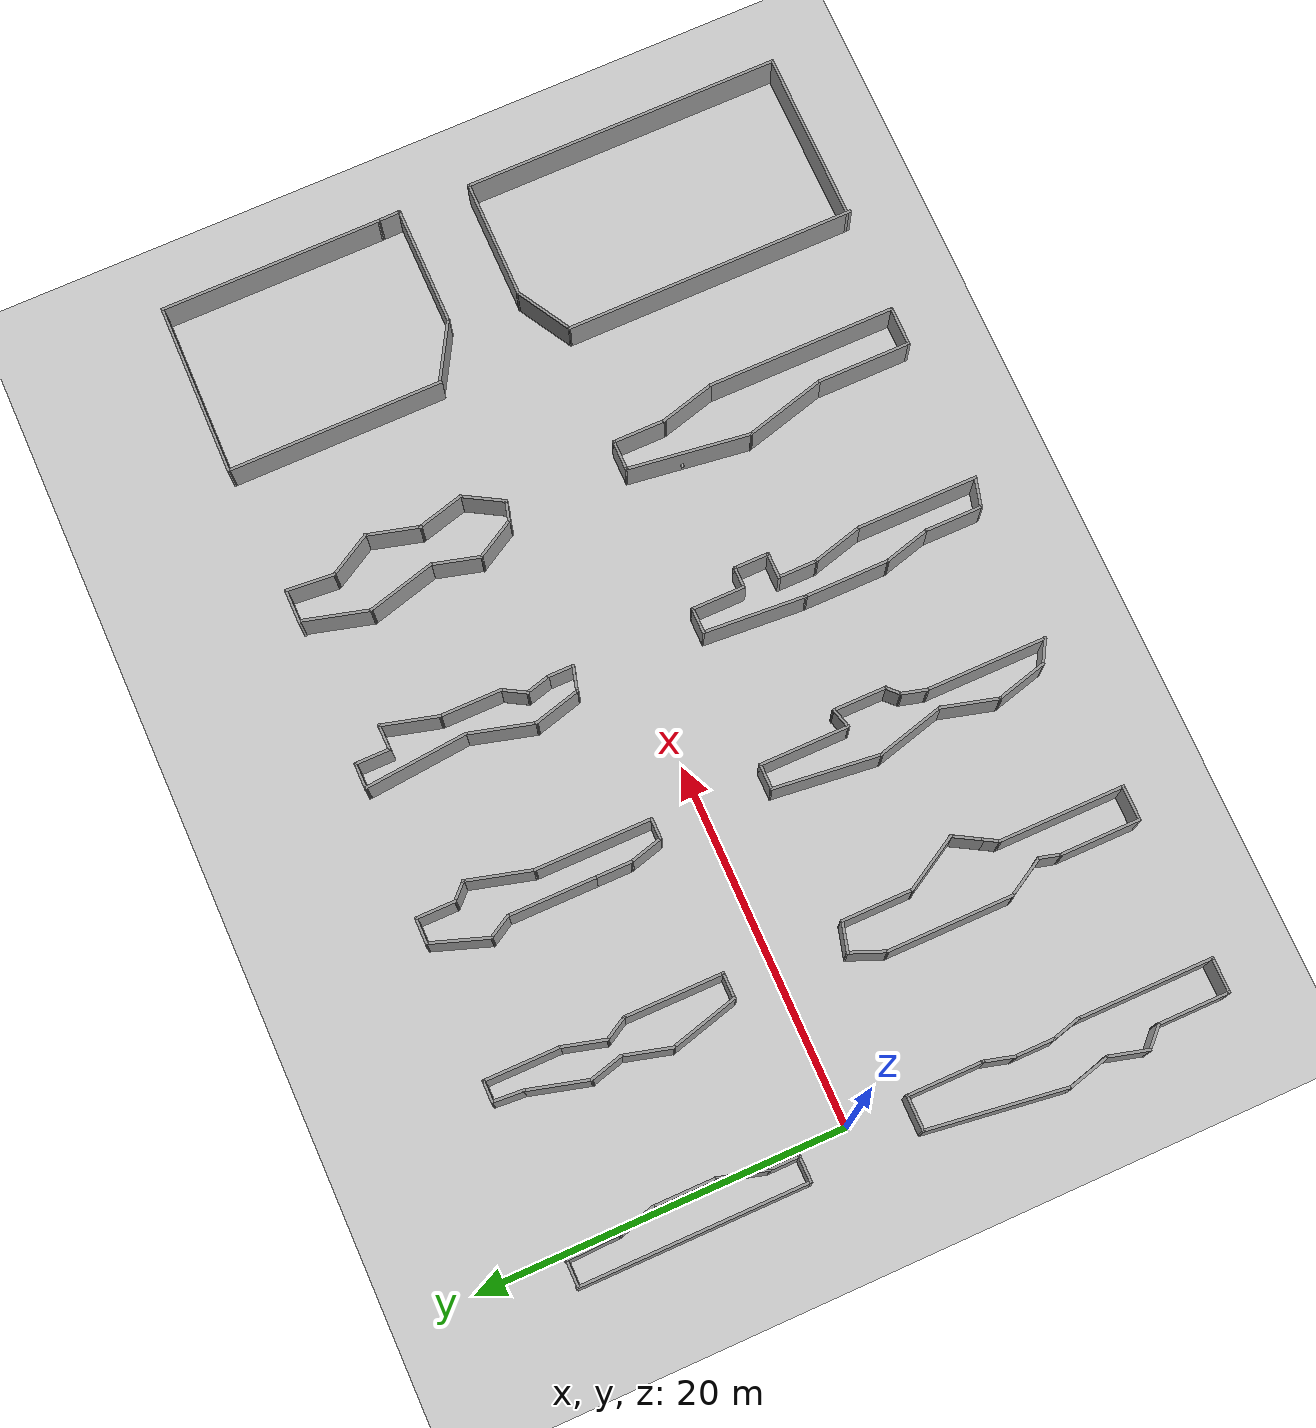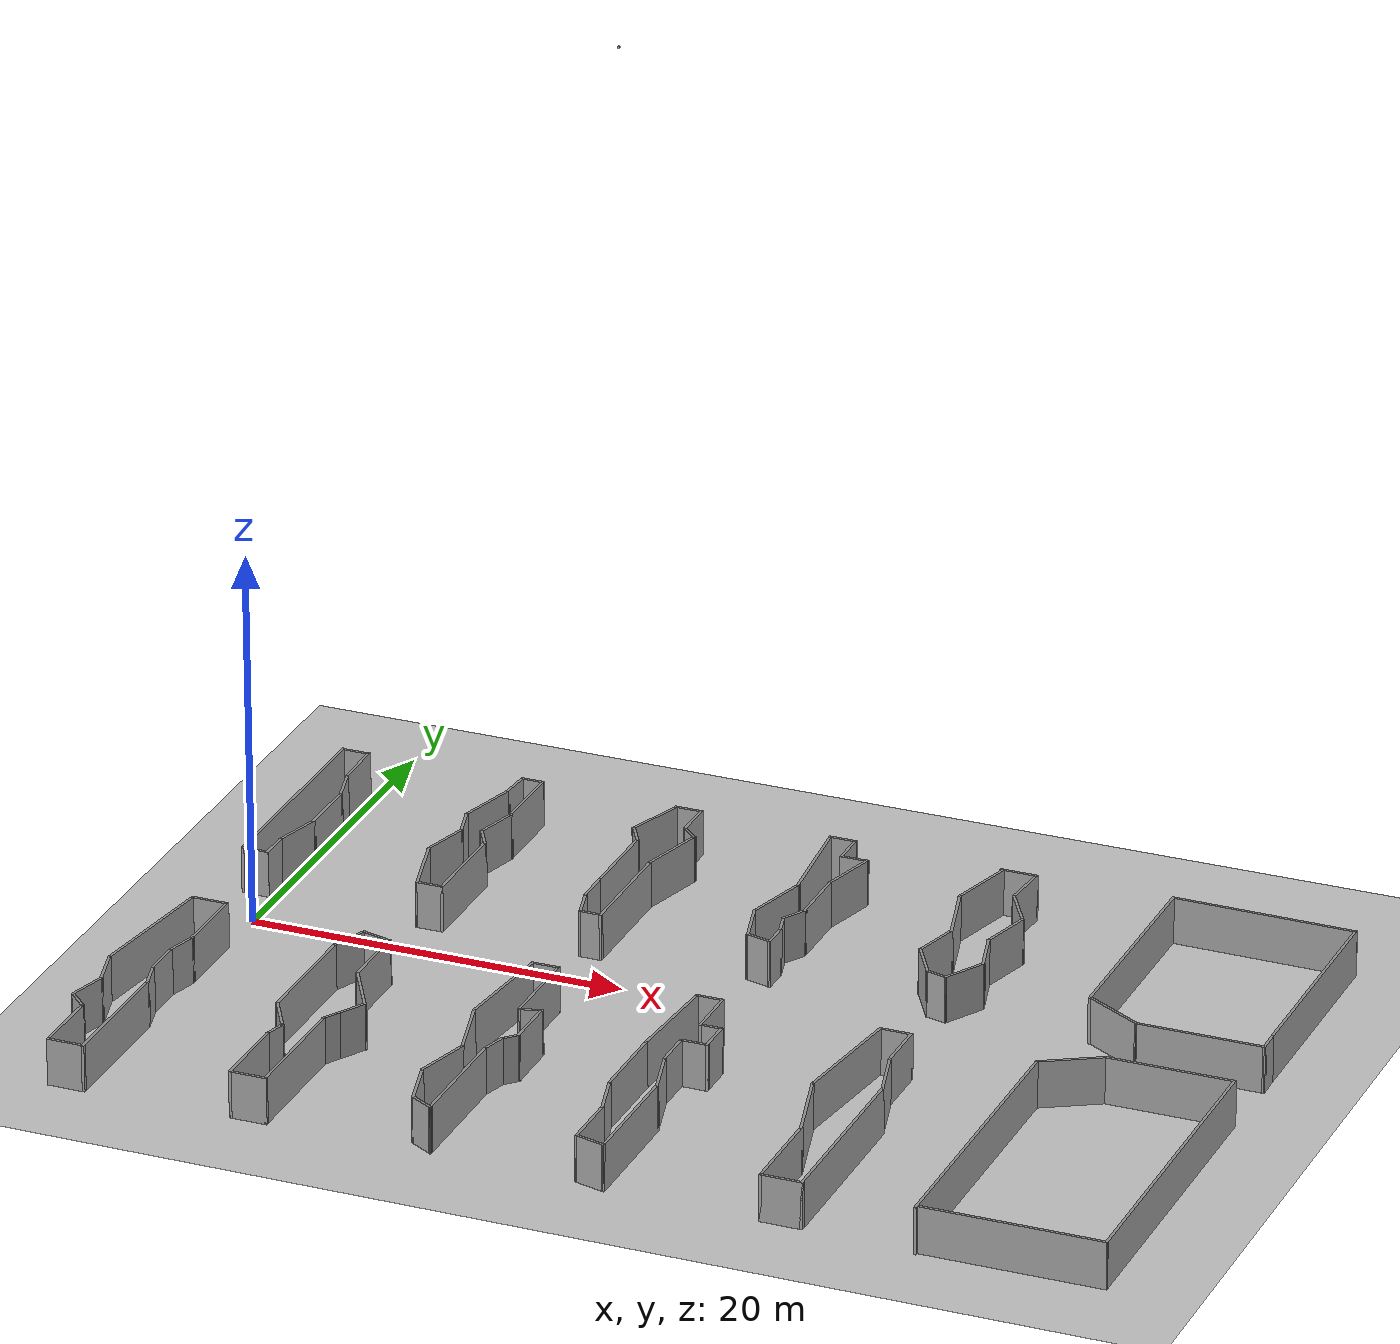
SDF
<sdf version="1.6">
 <world name="default">
  <light name="sun" type="directional">
   <pose>0 0 10 0 -0 0</pose>
   <diffuse>0.8 0.8 0.8 1</diffuse>
   <specular>0.1 0.1 0.1 1</specular>
   <attenuation>
    <range>1000</range>
    <constant>0.9</constant>
    <linear>0.01</linear>
    <quadratic>0.001</quadratic>
   </attenuation>
   <direction>-0.5 0.5 -1</direction>
  </light>
  <model name="camera">
   <link name="camera_link">
    <gravity>0</gravity>
    <pose>20 0.05 50 0 1.5 0</pose>
    <visual name="visual"><geometry><box><size>0.1 0.1 0.1</size></box></geometry></visual>
    <sensor name="camera" type="camera">
     <camera>
      <horizontal_fov>1.047</horizontal_fov>
      <image><width>2000</width><height>3000</height></image>
      <clip><near>0.1</near><far>100</far></clip>
      <save enabled="false"><path>/tmp</path></save>
     </camera>
     <plugin name="camera_controller" filename="libgazebo_ros_camera.so">
      <cameraName>gazebo/camera</cameraName>
      <imageTopicName>image_raw</imageTopicName>
     </plugin>
     <always_on>1</always_on>
     <update_rate>30</update_rate>
     <visualize>true</visualize>
    </sensor>
   </link>
  </model>
  <model name="ground_plane">
   <static>1</static>
   <link name="link">
    <collision name="collision">
     <geometry><plane><normal>0 0 1</normal><size>100 100</size></plane></geometry>
     <surface><friction><ode><mu>100</mu><mu2>50</mu2></ode></friction></surface>
    </collision>
    <visual name="visual">
     <cast_shadows>0</cast_shadows>
     <geometry><plane><normal>0 0 1</normal><size>100 100</size></plane></geometry>
     <material>
      <script><uri>file://media/materials/scripts/gazebo.material</uri><name>Gazebo/Grey</name></script>
     </material>
    </visual>
   </link>
  </model>
  <gravity>0 0 -9.8</gravity>
  <magnetic_field>6e-06 2.3e-05 -4.2e-05</magnetic_field>
  <atmosphere type="adiabatic"/>
  <physics name="default_physics" default="0" type="ode">
   <max_step_size>0.001</max_step_size>
   <real_time_factor>1</real_time_factor>
   <real_time_update_rate>1000</real_time_update_rate>
  </physics>
  <scene><ambient>0.4 0.4 0.4 1</ambient><background>0.7 0.7 0.7 1</background><shadows>1</shadows></scene>
  <spherical_coordinates>
   <surface_model>EARTH_WGS84</surface_model>
   <latitude_deg>0</latitude_deg>
   <longitude_deg>0</longitude_deg>
   <elevation>0</elevation>
   <heading_deg>0</heading_deg>
  </spherical_coordinates>
  <model name="supermarket">
   <pose>25.0605 -2.27607 0 0 -0 0</pose>
   <link name="Wall_10">
    <collision name="Wall_10_Collision">
     <geometry><box><size>5.5 0.15 2.5</size></box></geometry>
     <pose>0 0 1.25 0 -0 0</pose>
    </collision>
    <visual name="Wall_10_Visual">
     <pose>0 0 1.25 0 -0 0</pose>
     <geometry><box><size>5.5 0.15 2.5</size></box></geometry>
     <material>
      <script><uri>file://media/materials/scripts/gazebo.material</uri><name>Gazebo/Grey</name></script>
      <ambient>1 1 1 1</ambient>
     </material>
     <meta><layer>0</layer></meta>
    </visual>
    <pose>-15.8473 7.53046 0 0 -0 1.5708</pose>
   </link>
   <link name="Wall_100">
    <collision name="Wall_100_Collision">
     <geometry><box><size>1.5 0.15 2.5</size></box></geometry>
     <pose>0 0 1.25 0 -0 0</pose>
    </collision>
    <visual name="Wall_100_Visual">
     <pose>0 0 1.25 0 -0 0</pose>
     <geometry><box><size>1.5 0.15 2.5</size></box></geometry>
     <material>
      <script><uri>file://media/materials/scripts/gazebo.material</uri><name>Gazebo/Grey</name></script>
      <ambient>1 1 1 1</ambient>
     </material>
     <meta><layer>0</layer></meta>
    </visual>
    <pose>2.20267 -6.05084 0 0 -0 3.14159</pose>
   </link>
   <link name="Wall_101">
    <collision name="Wall_101_Collision">
     <geometry><box><size>2.25 0.15 2.5</size></box></geometry>
     <pose>0 0 1.25 0 -0 0</pose>
    </collision>
    <visual name="Wall_101_Visual">
     <pose>0 0 1.25 0 -0 0</pose>
     <geometry><box><size>2.25 0.15 2.5</size></box></geometry>
     <material>
      <script><uri>file://media/materials/scripts/gazebo.material</uri><name>Gazebo/Grey</name></script>
      <ambient>1 1 1 1</ambient>
     </material>
     <meta><layer>0</layer></meta>
    </visual>
    <pose>1.52767 -7.10084 0 0 0 -1.5708</pose>
   </link>
   <link name="Wall_102">
    <collision name="Wall_102_Collision">
     <geometry><box><size>3 0.15 2.5</size></box></geometry>
     <pose>0 0 1.25 0 -0 0</pose>
    </collision>
    <visual name="Wall_102_Visual">
     <pose>0 0 1.25 0 -0 0</pose>
     <geometry><box><size>3 0.15 2.5</size></box></geometry>
     <material>
      <script><uri>file://media/materials/scripts/gazebo.material</uri><name>Gazebo/Grey</name></script>
      <ambient>1 1 1 1</ambient>
     </material>
     <meta><layer>0</layer></meta>
    </visual>
    <pose>1.89649 -9.52728 0 0 0 -1.309</pose>
   </link>
   <link name="Wall_103">
    <collision name="Wall_103_Collision">
     <geometry><box><size>6.75 0.15 2.5</size></box></geometry>
     <pose>0 0 1.25 0 -0 0</pose>
    </collision>
    <visual name="Wall_103_Visual">
     <pose>0 0 1.25 0 -0 0</pose>
     <geometry><box><size>6.75 0.15 2.5</size></box></geometry>
     <material>
      <script><uri>file://media/materials/scripts/gazebo.material</uri><name>Gazebo/Grey</name></script>
      <ambient>1 1 1 1</ambient>
     </material>
     <meta><layer>0</layer></meta>
    </visual>
    <pose>2.26531 -14.2037 0 0 0 -1.5708</pose>
   </link>
   <link name="Wall_104">
    <collision name="Wall_104_Collision">
     <geometry><box><size>1.75 0.15 2.5</size></box></geometry>
     <pose>0 0 1.25 0 -0 0</pose>
    </collision>
    <visual name="Wall_104_Visual">
     <pose>0 0 1.25 0 -0 0</pose>
     <geometry><box><size>1.75 0.15 2.5</size></box></geometry>
     <material>
      <script><uri>file://media/materials/scripts/gazebo.material</uri><name>Gazebo/Grey</name></script>
      <ambient>1 1 1 1</ambient>
     </material>
     <meta><layer>0</layer></meta>
    </visual>
    <pose>1.49256 -17.2967 0 0 -0 2.87979</pose>
   </link>
   <link name="Wall_105">
    <collision name="Wall_105_Collision">
     <geometry><box><size>3.25 0.15 2.5</size></box></geometry>
     <pose>0 0 1.25 0 -0 0</pose>
    </collision>
    <visual name="Wall_105_Visual">
     <pose>0 0 1.25 0 -0 0</pose>
     <geometry><box><size>3.25 0.15 2.5</size></box></geometry>
     <material>
      <script><uri>file://media/materials/scripts/gazebo.material</uri><name>Gazebo/Grey</name></script>
      <ambient>1 1 1 1</ambient>
     </material>
     <meta><layer>0</layer></meta>
    </visual>
    <pose>0.719824 -15.5396 0 0 -0 1.5708</pose>
   </link>
   <link name="Wall_106">
    <collision name="Wall_106_Collision">
     <geometry><box><size>2.75 0.15 2.5</size></box></geometry>
     <pose>0 0 1.25 0 -0 0</pose>
    </collision>
    <visual name="Wall_106_Visual">
     <pose>0 0 1.25 0 -0 0</pose>
     <geometry><box><size>2.75 0.15 2.5</size></box></geometry>
     <material>
      <script><uri>file://media/materials/scripts/gazebo.material</uri><name>Gazebo/Grey</name></script>
      <ambient>1 1 1 1</ambient>
     </material>
     <meta><layer>0</layer></meta>
    </visual>
    <pose>0.383359 -12.7339 0 0 -0 1.8326</pose>
   </link>
   <link name="Wall_107">
    <collision name="Wall_107_Collision">
     <geometry><box><size>4.75 0.15 2.5</size></box></geometry>
     <pose>0 0 1.25 0 -0 0</pose>
    </collision>
    <visual name="Wall_107_Visual">
     <pose>0 0 1.25 0 -0 0</pose>
     <geometry><box><size>4.75 0.15 2.5</size></box></geometry>
     <material>
      <script><uri>file://media/materials/scripts/gazebo.material</uri><name>Gazebo/Grey</name></script>
      <ambient>1 1 1 1</ambient>
     </material>
     <meta><layer>0</layer></meta>
    </visual>
    <pose>0.046895 -9.17821 0 0 -0 1.5708</pose>
   </link>
   <link name="Wall_108">
    <collision name="Wall_108_Collision">
     <geometry><box><size>5.69047 0.15 2.5</size></box></geometry>
     <pose>0 0 1.25 0 -0 0</pose>
    </collision>
    <visual name="Wall_108_Visual">
     <pose>0 0 1.25 0 -0 0</pose>
     <geometry><box><size>5.69047 0.15 2.5</size></box></geometry>
     <material>
      <script><uri>file://media/materials/scripts/gazebo.material</uri><name>Gazebo/Grey</name></script>
      <ambient>1 1 1 1</ambient>
     </material>
     <meta><layer>0</layer></meta>
    </visual>
    <pose>0.237283 -4.11452 0 0 -0 1.50202</pose>
   </link>
   <link name="Wall_11">
    <collision name="Wall_11_Collision">
     <geometry><box><size>1.5 0.15 2.5</size></box></geometry>
     <pose>0 0 1.25 0 -0 0</pose>
    </collision>
    <visual name="Wall_11_Visual">
     <pose>0 0 1.25 0 -0 0</pose>
     <geometry><box><size>1.5 0.15 2.5</size></box></geometry>
     <material>
      <script><uri>file://media/materials/scripts/gazebo.material</uri><name>Gazebo/Grey</name></script>
      <ambient>1 1 1 1</ambient>
     </material>
     <meta><layer>0</layer></meta>
    </visual>
    <pose>-16.1848 10.79 0 0 -0 2.0944</pose>
   </link>
   <link name="Wall_112">
    <collision name="Wall_112_Collision">
     <geometry><box><size>2 0.15 2.5</size></box></geometry>
     <pose>0 0 1.25 0 -0 0</pose>
    </collision>
    <visual name="Wall_112_Visual">
     <pose>0 0 1.25 0 -0 0</pose>
     <geometry><box><size>2 0.15 2.5</size></box></geometry>
     <material>
      <script><uri>file://media/materials/scripts/gazebo.material</uri><name>Gazebo/Grey</name></script>
      <ambient>1 1 1 1</ambient>
     </material>
     <meta><layer>0</layer></meta>
    </visual>
    <pose>10.1554 17.2151 0 0 -0 0</pose>
   </link>
   <link name="Wall_113">
    <collision name="Wall_113_Collision">
     <geometry><box><size>2.68973 0.15 2.5</size></box></geometry>
     <pose>0 0 1.25 0 -0 0</pose>
    </collision>
    <visual name="Wall_113_Visual">
     <pose>0 0 1.25 0 -0 0</pose>
     <geometry><box><size>2.68973 0.15 2.5</size></box></geometry>
     <material>
      <script><uri>file://media/materials/scripts/gazebo.material</uri><name>Gazebo/Grey</name></script>
      <ambient>1 1 1 1</ambient>
     </material>
     <meta><layer>0</layer></meta>
    </visual>
    <pose>10.974 15.8965 0 0 0 -1.65468</pose>
   </link>
   <link name="Wall_114">
    <collision name="Wall_114_Collision">
     <geometry><box><size>2.75 0.15 2.5</size></box></geometry>
     <pose>0 0 1.25 0 -0 0</pose>
    </collision>
    <visual name="Wall_114_Visual">
     <pose>0 0 1.25 0 -0 0</pose>
     <geometry><box><size>2.75 0.15 2.5</size></box></geometry>
     <material>
      <script><uri>file://media/materials/scripts/gazebo.material</uri><name>Gazebo/Grey</name></script>
      <ambient>1 1 1 1</ambient>
     </material>
     <meta><layer>0</layer></meta>
    </visual>
    <pose>11.5176 13.5053 0 0 0 -1.0472</pose>
   </link>
   <link name="Wall_115">
    <collision name="Wall_115_Collision">
     <geometry><box><size>3 0.15 2.5</size></box></geometry>
     <pose>0 0 1.25 0 -0 0</pose>
    </collision>
    <visual name="Wall_115_Visual">
     <pose>0 0 1.25 0 -0 0</pose>
     <geometry><box><size>3 0.15 2.5</size></box></geometry>
     <material>
      <script><uri>file://media/materials/scripts/gazebo.material</uri><name>Gazebo/Grey</name></script>
      <ambient>1 1 1 1</ambient>
     </material>
     <meta><layer>0</layer></meta>
    </visual>
    <pose>11.7988 11.003 0 0 0 -1.8326</pose>
   </link>
   <link name="Wall_116">
    <collision name="Wall_116_Collision">
     <geometry><box><size>2.75 0.15 2.5</size></box></geometry>
     <pose>0 0 1.25 0 -0 0</pose>
    </collision>
    <visual name="Wall_116_Visual">
     <pose>0 0 1.25 0 -0 0</pose>
     <geometry><box><size>2.75 0.15 2.5</size></box></geometry>
     <material>
      <script><uri>file://media/materials/scripts/gazebo.material</uri><name>Gazebo/Grey</name></script>
      <ambient>1 1 1 1</ambient>
     </material>
     <meta><layer>0</layer></meta>
    </visual>
    <pose>11.7664 8.37086 0 0 0 -1.309</pose>
   </link>
   <link name="Wall_117">
    <collision name="Wall_117_Collision">
     <geometry><box><size>2.5 0.15 2.5</size></box></geometry>
     <pose>0 0 1.25 0 -0 0</pose>
    </collision>
    <visual name="Wall_117_Visual">
     <pose>0 0 1.25 0 -0 0</pose>
     <geometry><box><size>2.5 0.15 2.5</size></box></geometry>
     <material>
      <script><uri>file://media/materials/scripts/gazebo.material</uri><name>Gazebo/Grey</name></script>
      <ambient>1 1 1 1</ambient>
     </material>
     <meta><layer>0</layer></meta>
    </visual>
    <pose>11.5154 6.09758 0 0 0 -2.0944</pose>
   </link>
   <link name="Wall_118">
    <collision name="Wall_118_Collision">
     <geometry><box><size>1.25 0.15 2.5</size></box></geometry>
     <pose>0 0 1.25 0 -0 0</pose>
    </collision>
    <visual name="Wall_118_Visual">
     <pose>0 0 1.25 0 -0 0</pose>
     <geometry><box><size>1.25 0.15 2.5</size></box></geometry>
     <material>
      <script><uri>file://media/materials/scripts/gazebo.material</uri><name>Gazebo/Grey</name></script>
      <ambient>1 1 1 1</ambient>
     </material>
     <meta><layer>0</layer></meta>
    </visual>
    <pose>10.3966 5.22235 0 0 -0 2.87979</pose>
   </link>
   <link name="Wall_119">
    <collision name="Wall_119_Collision">
     <geometry><box><size>2.5 0.15 2.5</size></box></geometry>
     <pose>0 0 1.25 0 -0 0</pose>
    </collision>
    <visual name="Wall_119_Visual">
     <pose>0 0 1.25 0 -0 0</pose>
     <geometry><box><size>2.5 0.15 2.5</size></box></geometry>
     <material>
      <script><uri>file://media/materials/scripts/gazebo.material</uri><name>Gazebo/Grey</name></script>
      <ambient>1 1 1 1</ambient>
     </material>
     <meta><layer>0</layer></meta>
    </visual>
    <pose>9.27785 6.38228 0 0 -0 2.0944</pose>
   </link>
   <link name="Wall_12">
    <collision name="Wall_12_Collision">
     <geometry><box><size>2.5 0.15 2.5</size></box></geometry>
     <pose>0 0 1.25 0 -0 0</pose>
    </collision>
    <visual name="Wall_12_Visual">
     <pose>0 0 1.25 0 -0 0</pose>
     <geometry><box><size>2.5 0.15 2.5</size></box></geometry>
     <material>
      <script><uri>file://media/materials/scripts/gazebo.material</uri><name>Gazebo/Grey</name></script>
      <ambient>1 1 1 1</ambient>
     </material>
     <meta><layer>0</layer></meta>
    </visual>
    <pose>-16.2182 12.5096 0 0 -0 1.309</pose>
   </link>
   <link name="Wall_120">
    <collision name="Wall_120_Collision">
     <geometry><box><size>2.75 0.15 2.5</size></box></geometry>
     <pose>0 0 1.25 0 -0 0</pose>
    </collision>
    <visual name="Wall_120_Visual">
     <pose>0 0 1.25 0 -0 0</pose>
     <geometry><box><size>2.75 0.15 2.5</size></box></geometry>
     <material>
      <script><uri>file://media/materials/scripts/gazebo.material</uri><name>Gazebo/Grey</name></script>
      <ambient>1 1 1 1</ambient>
     </material>
     <meta><layer>0</layer></meta>
    </visual>
    <pose>9.02682 8.65556 0 0 -0 1.309</pose>
   </link>
   <link name="Wall_121">
    <collision name="Wall_121_Collision">
     <geometry><box><size>4 0.15 2.5</size></box></geometry>
     <pose>0 0 1.25 0 -0 0</pose>
    </collision>
    <visual name="Wall_121_Visual">
     <pose>0 0 1.25 0 -0 0</pose>
     <geometry><box><size>4 0.15 2.5</size></box></geometry>
     <material>
      <script><uri>file://media/materials/scripts/gazebo.material</uri><name>Gazebo/Grey</name></script>
      <ambient>1 1 1 1</ambient>
     </material>
     <meta><layer>0</layer></meta>
    </visual>
    <pose>8.86506 11.7707 0 0 -0 1.8326</pose>
   </link>
   <link name="Wall_122">
    <collision name="Wall_122_Collision">
     <geometry><box><size>3.75 0.15 2.5</size></box></geometry>
     <pose>0 0 1.25 0 -0 0</pose>
    </collision>
    <visual name="Wall_122_Visual">
     <pose>0 0 1.25 0 -0 0</pose>
     <geometry><box><size>3.75 0.15 2.5</size></box></geometry>
     <material>
      <script><uri>file://media/materials/scripts/gazebo.material</uri><name>Gazebo/Grey</name></script>
      <ambient>1 1 1 1</ambient>
     </material>
     <meta><layer>0</layer></meta>
    </visual>
    <pose>8.83271 15.3687 0 0 -0 1.309</pose>
   </link>
   <link name="Wall_124">
    <collision name="Wall_124_Collision">
     <geometry><box><size>1.75 0.15 2.5</size></box></geometry>
     <pose>0 0 1.25 0 -0 0</pose>
    </collision>
    <visual name="Wall_124_Visual">
     <pose>0 0 1.25 0 -0 0</pose>
     <geometry><box><size>1.75 0.15 2.5</size></box></geometry>
     <material>
      <script><uri>file://media/materials/scripts/gazebo.material</uri><name>Gazebo/Grey</name></script>
      <ambient>1 1 1 1</ambient>
     </material>
     <meta><layer>0</layer></meta>
    </visual>
    <pose>10.7924 -1.2652 0 0 -0 0</pose>
   </link>
   <link name="Wall_125">
    <collision name="Wall_125_Collision">
     <geometry><box><size>3 0.15 2.5</size></box></geometry>
     <pose>0 0 1.25 0 -0 0</pose>
    </collision>
    <visual name="Wall_125_Visual">
     <pose>0 0 1.25 0 -0 0</pose>
     <geometry><box><size>3 0.15 2.5</size></box></geometry>
     <material>
      <script><uri>file://media/materials/scripts/gazebo.material</uri><name>Gazebo/Grey</name></script>
      <ambient>1 1 1 1</ambient>
     </material>
     <meta><layer>0</layer></meta>
    </visual>
    <pose>11.5924 -2.6902 0 0 0 -1.5708</pose>
   </link>
   <link name="Wall_126">
    <collision name="Wall_126_Collision">
     <geometry><box><size>3.25 0.15 2.5</size></box></geometry>
     <pose>0 0 1.25 0 -0 0</pose>
    </collision>
    <visual name="Wall_126_Visual">
     <pose>0 0 1.25 0 -0 0</pose>
     <geometry><box><size>3.25 0.15 2.5</size></box></geometry>
     <material>
      <script><uri>file://media/materials/scripts/gazebo.material</uri><name>Gazebo/Grey</name></script>
      <ambient>1 1 1 1</ambient>
     </material>
     <meta><layer>0</layer></meta>
    </visual>
    <pose>11.9935 -5.61238 0 0 0 -1.309</pose>
   </link>
   <link name="Wall_127">
    <collision name="Wall_127_Collision">
     <geometry><box><size>10.5 0.15 2.5</size></box></geometry>
     <pose>0 0 1.25 0 -0 0</pose>
    </collision>
    <visual name="Wall_127_Visual">
     <pose>0 0 1.25 0 -0 0</pose>
     <geometry><box><size>10.5 0.15 2.5</size></box></geometry>
     <material>
      <script><uri>file://media/materials/scripts/gazebo.material</uri><name>Gazebo/Grey</name></script>
      <ambient>1 1 1 1</ambient>
     </material>
     <meta><layer>0</layer></meta>
    </visual>
    <pose>12.3947 -12.2846 0 0 0 -1.5708</pose>
   </link>
   <link name="Wall_128">
    <collision name="Wall_128_Collision">
     <geometry><box><size>2.25 0.15 2.5</size></box></geometry>
     <pose>0 0 1.25 0 -0 0</pose>
    </collision>
    <visual name="Wall_128_Visual">
     <pose>0 0 1.25 0 -0 0</pose>
     <geometry><box><size>2.25 0.15 2.5</size></box></geometry>
     <material>
      <script><uri>file://media/materials/scripts/gazebo.material</uri><name>Gazebo/Grey</name></script>
      <ambient>1 1 1 1</ambient>
     </material>
     <meta><layer>0</layer></meta>
    </visual>
    <pose>11.3447 -17.4596 0 0 -0 3.14159</pose>
   </link>
   <link name="Wall_129">
    <collision name="Wall_129_Collision">
     <geometry><box><size>5.25 0.15 2.5</size></box></geometry>
     <pose>0 0 1.25 0 -0 0</pose>
    </collision>
    <visual name="Wall_129_Visual">
     <pose>0 0 1.25 0 -0 0</pose>
     <geometry><box><size>5.25 0.15 2.5</size></box></geometry>
     <material>
      <script><uri>file://media/materials/scripts/gazebo.material</uri><name>Gazebo/Grey</name></script>
      <ambient>1 1 1 1</ambient>
     </material>
     <meta><layer>0</layer></meta>
    </visual>
    <pose>10.2947 -14.9096 0 0 -0 1.5708</pose>
   </link>
   <link name="Wall_13">
    <collision name="Wall_13_Collision">
     <geometry><box><size>4.25 0.15 2.5</size></box></geometry>
     <pose>0 0 1.25 0 -0 0</pose>
    </collision>
    <visual name="Wall_13_Visual">
     <pose>0 0 1.25 0 -0 0</pose>
     <geometry><box><size>4.25 0.15 2.5</size></box></geometry>
     <material>
      <script><uri>file://media/materials/scripts/gazebo.material</uri><name>Gazebo/Grey</name></script>
      <ambient>1 1 1 1</ambient>
     </material>
     <meta><layer>0</layer></meta>
    </visual>
    <pose>-15.9141 15.6945 0 0 -0 1.5708</pose>
   </link>
   <link name="Wall_130">
    <collision name="Wall_130_Collision">
     <geometry><box><size>4.75 0.15 2.5</size></box></geometry>
     <pose>0 0 1.25 0 -0 0</pose>
    </collision>
    <visual name="Wall_130_Visual">
     <pose>0 0 1.25 0 -0 0</pose>
     <geometry><box><size>4.75 0.15 2.5</size></box></geometry>
     <material>
      <script><uri>file://media/materials/scripts/gazebo.material</uri><name>Gazebo/Grey</name></script>
      <ambient>1 1 1 1</ambient>
     </material>
     <meta><layer>0</layer></meta>
    </visual>
    <pose>9.69942 -10.1379 0 0 -0 1.8326</pose>
   </link>
   <link name="Wall_131">
    <collision name="Wall_131_Collision">
     <geometry><box><size>6.86016 0.15 2.5</size></box></geometry>
     <pose>0 0 1.25 0 -0 0</pose>
    </collision>
    <visual name="Wall_131_Visual">
     <pose>0 0 1.25 0 -0 0</pose>
     <geometry><box><size>6.86016 0.15 2.5</size></box></geometry>
     <material>
      <script><uri>file://media/materials/scripts/gazebo.material</uri><name>Gazebo/Grey</name></script>
      <ambient>1 1 1 1</ambient>
     </material>
     <meta><layer>0</layer></meta>
    </visual>
    <pose>9.54825 -4.59075 0 0 -0 1.43804</pose>
   </link>
   <link name="Wall_135">
    <collision name="Wall_135_Collision">
     <geometry><box><size>12.3776 0.15 2.5</size></box></geometry>
     <pose>0 0 1.25 0 -0 0</pose>
    </collision>
    <visual name="Wall_135_Visual">
     <pose>0 0 1.25 0 -0 0</pose>
     <geometry><box><size>12.3776 0.15 2.5</size></box></geometry>
     <material>
      <script><uri>file://media/materials/scripts/gazebo.material</uri><name>Gazebo/Grey</name></script>
      <ambient>1 1 1 1</ambient>
     </material>
     <meta><layer>0</layer></meta>
    </visual>
    <pose>27.8396 11.2672 0 0 -0 1.5708</pose>
   </link>
   <link name="Wall_136">
    <collision name="Wall_136_Collision">
     <geometry><box><size>9.75 0.15 2.5</size></box></geometry>
     <pose>0 0 1.25 0 -0 0</pose>
    </collision>
    <visual name="Wall_136_Visual">
     <pose>0 0 1.25 0 -0 0</pose>
     <geometry><box><size>9.75 0.15 2.5</size></box></geometry>
     <material>
      <script><uri>file://media/materials/scripts/gazebo.material</uri><name>Gazebo/Grey</name></script>
      <ambient>1 1 1 1</ambient>
     </material>
     <meta><layer>0</layer></meta>
    </visual>
    <pose>23.0396 17.4422 0 0 -0 3.12885</pose>
   </link>
   <link name="Wall_14">
    <collision name="Wall_14_Collision">
     <geometry><box><size>1.25 0.15 2.5</size></box></geometry>
     <pose>0 0 1.25 0 -0 0</pose>
    </collision>
    <visual name="Wall_14_Visual">
     <pose>0 0 1.25 0 -0 0</pose>
     <geometry><box><size>1.25 0.15 2.5</size></box></geometry>
     <material>
      <script><uri>file://media/materials/scripts/gazebo.material</uri><name>Gazebo/Grey</name></script>
      <ambient>1 1 1 1</ambient>
     </material>
     <meta><layer>0</layer></meta>
    </visual>
    <pose>-16.4641 17.7445 0 0 -0 3.14159</pose>
   </link>
   <link name="Wall_140">
    <collision name="Wall_140_Collision">
     <geometry><box><size>3.5 0.15 2.5</size></box></geometry>
     <pose>0 0 1.25 0 -0 0</pose>
    </collision>
    <visual name="Wall_140_Visual">
     <pose>0 0 1.25 0 -0 0</pose>
     <geometry><box><size>3.5 0.15 2.5</size></box></geometry>
     <material>
      <script><uri>file://media/materials/scripts/gazebo.material</uri><name>Gazebo/Grey</name></script>
      <ambient>1 1 1 1</ambient>
     </material>
     <meta><layer>0</layer></meta>
    </visual>
    <pose>19.8164 4.79323 0 0 0 -0.523599</pose>
   </link>
   <link name="Wall_141">
    <collision name="Wall_141_Collision">
     <geometry><box><size>6.75 0.15 2.5</size></box></geometry>
     <pose>0 0 1.25 0 -0 0</pose>
    </collision>
    <visual name="Wall_141_Visual">
     <pose>0 0 1.25 0 -0 0</pose>
     <geometry><box><size>6.75 0.15 2.5</size></box></geometry>
     <material>
      <script><uri>file://media/materials/scripts/gazebo.material</uri><name>Gazebo/Grey</name></script>
      <ambient>1 1 1 1</ambient>
     </material>
     <meta><layer>0</layer></meta>
    </visual>
    <pose>24.567 3.95573 0 0 -0 0</pose>
   </link>
   <link name="Wall_142">
    <collision name="Wall_142_Collision">
     <geometry><box><size>1.348 0.15 2.5</size></box></geometry>
     <pose>0 0 1.25 0 -0 0</pose>
    </collision>
    <visual name="Wall_142_Visual">
     <pose>0 0 1.25 0 -0 0</pose>
     <geometry><box><size>1.348 0.15 2.5</size></box></geometry>
     <material>
      <script><uri>file://media/materials/scripts/gazebo.material</uri><name>Gazebo/Grey</name></script>
      <ambient>1 1 1 1</ambient>
     </material>
     <meta><layer>0</layer></meta>
    </visual>
    <pose>27.8533 4.55457 0 0 -0 1.59368</pose>
   </link>
   <link name="Wall_144">
    <collision name="Wall_144_Collision">
     <geometry><box><size>3.5 0.15 2.5</size></box></geometry>
     <pose>0 0 1.25 0 -0 0</pose>
    </collision>
    <visual name="Wall_144_Visual">
     <pose>0 0 1.25 0 -0 0</pose>
     <geometry><box><size>3.5 0.15 2.5</size></box></geometry>
     <material>
      <script><uri>file://media/materials/scripts/gazebo.material</uri><name>Gazebo/Grey</name></script>
      <ambient>1 1 1 1</ambient>
     </material>
     <meta><layer>0</layer></meta>
    </visual>
    <pose>19.6941 -0.812247 0 0 -0 0.523599</pose>
   </link>
   <link name="Wall_145">
    <collision name="Wall_145_Collision">
     <geometry><box><size>6.75 0.15 2.5</size></box></geometry>
     <pose>0 0 1.25 0 -0 0</pose>
    </collision>
    <visual name="Wall_145_Visual">
     <pose>0 0 1.25 0 -0 0</pose>
     <geometry><box><size>6.75 0.15 2.5</size></box></geometry>
     <material>
      <script><uri>file://media/materials/scripts/gazebo.material</uri><name>Gazebo/Grey</name></script>
      <ambient>1 1 1 1</ambient>
     </material>
     <meta><layer>0</layer></meta>
    </visual>
    <pose>24.4447 0.025253 0 0 -0 0</pose>
   </link>
   <link name="Wall_146">
    <collision name="Wall_146_Collision">
     <geometry><box><size>17.75 0.15 2.5</size></box></geometry>
     <pose>0 0 1.25 0 -0 0</pose>
    </collision>
    <visual name="Wall_146_Visual">
     <pose>0 0 1.25 0 -0 0</pose>
     <geometry><box><size>17.75 0.15 2.5</size></box></geometry>
     <material>
      <script><uri>file://media/materials/scripts/gazebo.material</uri><name>Gazebo/Grey</name></script>
      <ambient>1 1 1 1</ambient>
     </material>
     <meta><layer>0</layer></meta>
    </visual>
    <pose>27.7447 -8.77475 0 0 0 -1.5708</pose>
   </link>
   <link name="Wall_147">
    <collision name="Wall_147_Collision">
     <geometry><box><size>9.65508 0.15 2.5</size></box></geometry>
     <pose>0 0 1.25 0 -0 0</pose>
    </collision>
    <visual name="Wall_147_Visual">
     <pose>0 0 1.25 0 -0 0</pose>
     <geometry><box><size>9.65508 0.15 2.5</size></box></geometry>
     <material>
      <script><uri>file://media/materials/scripts/gazebo.material</uri><name>Gazebo/Grey</name></script>
      <ambient>1 1 1 1</ambient>
     </material>
     <meta><layer>0</layer></meta>
    </visual>
    <pose>22.9921 -17.5857 0 0 0 -3.1393</pose>
   </link>
   <link name="Wall_149">
    <collision name="Wall_149_Collision">
     <geometry><box><size>12 0.15 2.5</size></box></geometry>
     <pose>0 0 1.25 0 -0 0</pose>
    </collision>
    <visual name="Wall_149_Visual">
     <pose>0 0 1.25 0 -0 0</pose>
     <geometry><box><size>12 0.15 2.5</size></box></geometry>
     <material>
      <script><uri>file://media/materials/scripts/gazebo.material</uri><name>Gazebo/Grey</name></script>
      <ambient>1 1 1 1</ambient>
     </material>
     <meta><layer>0</layer></meta>
    </visual>
    <pose>18.2396 11.5784 0 0 0 -1.5708</pose>
   </link>
   <link name="Wall_15">
    <collision name="Wall_15_Collision">
     <geometry><box><size>1.79031 0.15 2.5</size></box></geometry>
     <pose>0 0 1.25 0 -0 0</pose>
    </collision>
    <visual name="Wall_15_Visual">
     <pose>0 0 1.25 0 -0 0</pose>
     <geometry><box><size>1.79031 0.15 2.5</size></box></geometry>
     <material>
      <script><uri>file://media/materials/scripts/gazebo.material</uri><name>Gazebo/Grey</name></script>
      <ambient>1 1 1 1</ambient>
     </material>
     <meta><layer>0</layer></meta>
    </visual>
    <pose>-17.0734 16.9265 0 0 0 -1.64311</pose>
   </link>
   <link name="Wall_151">
    <collision name="Wall_151_Collision">
     <geometry><box><size>16.25 0.15 2.5</size></box></geometry>
     <pose>0 0 1.25 0 -0 0</pose>
    </collision>
    <visual name="Wall_151_Visual">
     <pose>0 0 1.25 0 -0 0</pose>
     <geometry><box><size>16.25 0.15 2.5</size></box></geometry>
     <material>
      <script><uri>file://media/materials/scripts/gazebo.material</uri><name>Gazebo/Grey</name></script>
      <ambient>1 1 1 1</ambient>
     </material>
     <meta><layer>0</layer></meta>
    </visual>
    <pose>18.2435 -9.69975 0 0 0 -1.5708</pose>
   </link>
   <link name="Wall_17">
    <collision name="Wall_17_Collision">
     <geometry><box><size>1.5 0.15 2.5</size></box></geometry>
     <pose>0 0 1.25 0 -0 0</pose>
    </collision>
    <visual name="Wall_17_Visual">
     <pose>0 0 1.25 0 -0 0</pose>
     <geometry><box><size>1.5 0.15 2.5</size></box></geometry>
     <material>
      <script><uri>file://media/materials/scripts/gazebo.material</uri><name>Gazebo/Grey</name></script>
      <ambient>1 1 1 1</ambient>
     </material>
     <meta><layer>0</layer></meta>
    </visual>
    <pose>-7.84293 17.6629 0 0 -0 0</pose>
   </link>
   <link name="Wall_18">
    <collision name="Wall_18_Collision">
     <geometry><box><size>2.25 0.15 2.5</size></box></geometry>
     <pose>0 0 1.25 0 -0 0</pose>
    </collision>
    <visual name="Wall_18_Visual">
     <pose>0 0 1.25 0 -0 0</pose>
     <geometry><box><size>2.25 0.15 2.5</size></box></geometry>
     <material>
      <script><uri>file://media/materials/scripts/gazebo.material</uri><name>Gazebo/Grey</name></script>
      <ambient>1 1 1 1</ambient>
     </material>
     <meta><layer>0</layer></meta>
    </visual>
    <pose>-7.16793 16.6129 0 0 0 -1.5708</pose>
   </link>
   <link name="Wall_19">
    <collision name="Wall_19_Collision">
     <geometry><box><size>1.25 0.15 2.5</size></box></geometry>
     <pose>0 0 1.25 0 -0 0</pose>
    </collision>
    <visual name="Wall_19_Visual">
     <pose>0 0 1.25 0 -0 0</pose>
     <geometry><box><size>1.25 0.15 2.5</size></box></geometry>
     <material>
      <script><uri>file://media/materials/scripts/gazebo.material</uri><name>Gazebo/Grey</name></script>
      <ambient>1 1 1 1</ambient>
     </material>
     <meta><layer>0</layer></meta>
    </visual>
    <pose>-6.77902 15.174 0 0 0 -0.785398</pose>
   </link>
   <link name="Wall_20">
    <collision name="Wall_20_Collision">
     <geometry><box><size>3.75 0.15 2.5</size></box></geometry>
     <pose>0 0 1.25 0 -0 0</pose>
    </collision>
    <visual name="Wall_20_Visual">
     <pose>0 0 1.25 0 -0 0</pose>
     <geometry><box><size>3.75 0.15 2.5</size></box></geometry>
     <material>
      <script><uri>file://media/materials/scripts/gazebo.material</uri><name>Gazebo/Grey</name></script>
      <ambient>1 1 1 1</ambient>
     </material>
     <meta><layer>0</layer></meta>
    </visual>
    <pose>-6.85598 13.0464 0 0 0 -1.8326</pose>
   </link>
   <link name="Wall_21">
    <collision name="Wall_21_Collision">
     <geometry><box><size>6.5 0.15 2.5</size></box></geometry>
     <pose>0 0 1.25 0 -0 0</pose>
    </collision>
    <visual name="Wall_21_Visual">
     <pose>0 0 1.25 0 -0 0</pose>
     <geometry><box><size>6.5 0.15 2.5</size></box></geometry>
     <material>
      <script><uri>file://media/materials/scripts/gazebo.material</uri><name>Gazebo/Grey</name></script>
      <ambient>1 1 1 1</ambient>
     </material>
     <meta><layer>0</layer></meta>
    </visual>
    <pose>-7.32186 8.13277 0 0 0 -1.5708</pose>
   </link>
   <link name="Wall_22">
    <collision name="Wall_22_Collision">
     <geometry><box><size>1.25 0.15 2.5</size></box></geometry>
     <pose>0 0 1.25 0 -0 0</pose>
    </collision>
    <visual name="Wall_22_Visual">
     <pose>0 0 1.25 0 -0 0</pose>
     <geometry><box><size>1.25 0.15 2.5</size></box></geometry>
     <material>
      <script><uri>file://media/materials/scripts/gazebo.material</uri><name>Gazebo/Grey</name></script>
      <ambient>1 1 1 1</ambient>
     </material>
     <meta><layer>0</layer></meta>
    </visual>
    <pose>-7.87186 4.95777 0 0 -0 3.14159</pose>
   </link>
   <link name="Wall_23">
    <collision name="Wall_23_Collision">
     <geometry><box><size>2 0.15 2.5</size></box></geometry>
     <pose>0 0 1.25 0 -0 0</pose>
    </collision>
    <visual name="Wall_23_Visual">
     <pose>0 0 1.25 0 -0 0</pose>
     <geometry><box><size>2 0.15 2.5</size></box></geometry>
     <material>
      <script><uri>file://media/materials/scripts/gazebo.material</uri><name>Gazebo/Grey</name></script>
      <ambient>1 1 1 1</ambient>
     </material>
     <meta><layer>0</layer></meta>
    </visual>
    <pose>-8.66127 5.85125 0 0 -0 1.8326</pose>
   </link>
   <link name="Wall_24">
    <collision name="Wall_24_Collision">
     <geometry><box><size>2 0.15 2.5</size></box></geometry>
     <pose>0 0 1.25 0 -0 0</pose>
    </collision>
    <visual name="Wall_24_Visual">
     <pose>0 0 1.25 0 -0 0</pose>
     <geometry><box><size>2 0.15 2.5</size></box></geometry>
     <material>
      <script><uri>file://media/materials/scripts/gazebo.material</uri><name>Gazebo/Grey</name></script>
      <ambient>1 1 1 1</ambient>
     </material>
     <meta><layer>0</layer></meta>
    </visual>
    <pose>-8.90067 7.66973 0 0 -0 1.5708</pose>
   </link>
   <link name="Wall_25">
    <collision name="Wall_25_Collision">
     <geometry><box><size>5 0.15 2.5</size></box></geometry>
     <pose>0 0 1.25 0 -0 0</pose>
    </collision>
    <visual name="Wall_25_Visual">
     <pose>0 0 1.25 0 -0 0</pose>
     <geometry><box><size>5 0.15 2.5</size></box></geometry>
     <material>
      <script><uri>file://media/materials/scripts/gazebo.material</uri><name>Gazebo/Grey</name></script>
      <ambient>1 1 1 1</ambient>
     </material>
     <meta><layer>0</layer></meta>
    </visual>
    <pose>-8.90067 11.0197 0 0 -0 1.5708</pose>
   </link>
   <link name="Wall_26">
    <collision name="Wall_26_Collision">
     <geometry><box><size>1.5 0.15 2.5</size></box></geometry>
     <pose>0 0 1.25 0 -0 0</pose>
    </collision>
    <visual name="Wall_26_Visual">
     <pose>0 0 1.25 0 -0 0</pose>
     <geometry><box><size>1.5 0.15 2.5</size></box></geometry>
     <material>
      <script><uri>file://media/materials/scripts/gazebo.material</uri><name>Gazebo/Grey</name></script>
      <ambient>1 1 1 1</ambient>
     </material>
     <meta><layer>0</layer></meta>
    </visual>
    <pose>-9.23817 14.0293 0 0 -0 2.0944</pose>
   </link>
   <link name="Wall_27">
    <collision name="Wall_27_Collision">
     <geometry><box><size>3.37731 0.15 2.5</size></box></geometry>
     <pose>0 0 1.25 0 -0 0</pose>
    </collision>
    <visual name="Wall_27_Visual">
     <pose>0 0 1.25 0 -0 0</pose>
     <geometry><box><size>3.37731 0.15 2.5</size></box></geometry>
     <material>
      <script><uri>file://media/materials/scripts/gazebo.material</uri><name>Gazebo/Grey</name></script>
      <ambient>1 1 1 1</ambient>
     </material>
     <meta><layer>0</layer></meta>
    </visual>
    <pose>-9.0468 16.1384 0 0 -0 1.23688</pose>
   </link>
   <link name="Wall_30">
    <collision name="Wall_30_Collision">
     <geometry><box><size>1.5 0.15 2.5</size></box></geometry>
     <pose>0 0 1.25 0 -0 0</pose>
    </collision>
    <visual name="Wall_30_Visual">
     <pose>0 0 1.25 0 -0 0</pose>
     <geometry><box><size>1.5 0.15 2.5</size></box></geometry>
     <material>
      <script><uri>file://media/materials/scripts/gazebo.material</uri><name>Gazebo/Grey</name></script>
      <ambient>1 1 1 1</ambient>
     </material>
     <meta><layer>0</layer></meta>
    </visual>
    <pose>-26.1222 17.4347 0 0 -0 0</pose>
   </link>
   <link name="Wall_31">
    <collision name="Wall_31_Collision">
     <geometry><box><size>3.00977 0.15 2.5</size></box></geometry>
     <pose>0 0 1.25 0 -0 0</pose>
    </collision>
    <visual name="Wall_31_Visual">
     <pose>0 0 1.25 0 -0 0</pose>
     <geometry><box><size>3.00977 0.15 2.5</size></box></geometry>
     <material>
      <script><uri>file://media/materials/scripts/gazebo.material</uri><name>Gazebo/Grey</name></script>
      <ambient>1 1 1 1</ambient>
     </material>
     <meta><layer>0</layer></meta>
    </visual>
    <pose>-25.407 16.0456 0 0 0 -1.54266</pose>
   </link>
   <link name="Wall_32">
    <collision name="Wall_32_Collision">
     <geometry><box><size>2.25 0.15 2.5</size></box></geometry>
     <pose>0 0 1.25 0 -0 0</pose>
    </collision>
    <visual name="Wall_32_Visual">
     <pose>0 0 1.25 0 -0 0</pose>
     <geometry><box><size>2.25 0.15 2.5</size></box></geometry>
     <material>
      <script><uri>file://media/materials/scripts/gazebo.material</uri><name>Gazebo/Grey</name></script>
      <ambient>1 1 1 1</ambient>
     </material>
     <meta><layer>0</layer></meta>
    </visual>
    <pose>-25.095 13.6021 0 0 0 -1.309</pose>
   </link>
   <link name="Wall_33">
    <collision name="Wall_33_Collision">
     <geometry><box><size>3.5 0.15 2.5</size></box></geometry>
     <pose>0 0 1.25 0 -0 0</pose>
    </collision>
    <visual name="Wall_33_Visual">
     <pose>0 0 1.25 0 -0 0</pose>
     <geometry><box><size>3.5 0.15 2.5</size></box></geometry>
     <material>
      <script><uri>file://media/materials/scripts/gazebo.material</uri><name>Gazebo/Grey</name></script>
      <ambient>1 1 1 1</ambient>
     </material>
     <meta><layer>0</layer></meta>
    </visual>
    <pose>-24.8233 10.9128 0 0 0 -1.5708</pose>
   </link>
   <link name="Wall_34">
    <collision name="Wall_34_Collision">
     <geometry><box><size>2.75 0.15 2.5</size></box></geometry>
     <pose>0 0 1.25 0 -0 0</pose>
    </collision>
    <visual name="Wall_34_Visual">
     <pose>0 0 1.25 0 -0 0</pose>
     <geometry><box><size>2.75 0.15 2.5</size></box></geometry>
     <material>
      <script><uri>file://media/materials/scripts/gazebo.material</uri><name>Gazebo/Grey</name></script>
      <ambient>1 1 1 1</ambient>
     </material>
     <meta><layer>0</layer></meta>
    </visual>
    <pose>-25.1597 7.98213 0 0 0 -1.8326</pose>
   </link>
   <link name="Wall_36">
    <collision name="Wall_36_Collision">
     <geometry><box><size>1.75 0.15 2.5</size></box></geometry>
     <pose>0 0 1.25 0 -0 0</pose>
    </collision>
    <visual name="Wall_36_Visual">
     <pose>0 0 1.25 0 -0 0</pose>
     <geometry><box><size>1.75 0.15 2.5</size></box></geometry>
     <material>
      <script><uri>file://media/materials/scripts/gazebo.material</uri><name>Gazebo/Grey</name></script>
      <ambient>1 1 1 1</ambient>
     </material>
     <meta><layer>0</layer></meta>
    </visual>
    <pose>-25.4962 5.92643 0 0 0 -1.5708</pose>
   </link>
   <link name="Wall_37">
    <collision name="Wall_37_Collision">
     <geometry><box><size>1.5 0.15 2.5</size></box></geometry>
     <pose>0 0 1.25 0 -0 0</pose>
    </collision>
    <visual name="Wall_37_Visual">
     <pose>0 0 1.25 0 -0 0</pose>
     <geometry><box><size>1.5 0.15 2.5</size></box></geometry>
     <material>
      <script><uri>file://media/materials/scripts/gazebo.material</uri><name>Gazebo/Grey</name></script>
      <ambient>1 1 1 1</ambient>
     </material>
     <meta><layer>0</layer></meta>
    </visual>
    <pose>-26.1712 5.12643 0 0 -0 3.14159</pose>
   </link>
   <link name="Wall_38">
    <collision name="Wall_38_Collision">
     <geometry><box><size>12.5 0.15 2.5</size></box></geometry>
     <pose>0 0 1.25 0 -0 0</pose>
    </collision>
    <visual name="Wall_38_Visual">
     <pose>0 0 1.25 0 -0 0</pose>
     <geometry><box><size>12.5 0.15 2.5</size></box></geometry>
     <material>
      <script><uri>file://media/materials/scripts/gazebo.material</uri><name>Gazebo/Grey</name></script>
      <ambient>1 1 1 1</ambient>
     </material>
     <meta><layer>0</layer></meta>
    </visual>
    <pose>-26.8462 11.3014 0 0 -0 1.5708</pose>
   </link>
   <link name="Wall_40">
    <collision name="Wall_40_Collision">
     <geometry><box><size>2 0.15 2.5</size></box></geometry>
     <pose>0 0 1.25 0 -0 0</pose>
    </collision>
    <visual name="Wall_40_Visual">
     <pose>0 0 1.25 0 -0 0</pose>
     <geometry><box><size>2 0.15 2.5</size></box></geometry>
     <material>
      <script><uri>file://media/materials/scripts/gazebo.material</uri><name>Gazebo/Grey</name></script>
      <ambient>1 1 1 1</ambient>
     </material>
     <meta><layer>0</layer></meta>
    </visual>
    <pose>-25.9076 -0.905538 0 0 -0 0</pose>
   </link>
   <link name="Wall_41">
    <collision name="Wall_41_Collision">
     <geometry><box><size>4.25 0.15 2.5</size></box></geometry>
     <pose>0 0 1.25 0 -0 0</pose>
    </collision>
    <visual name="Wall_41_Visual">
     <pose>0 0 1.25 0 -0 0</pose>
     <geometry><box><size>4.25 0.15 2.5</size></box></geometry>
     <material>
      <script><uri>file://media/materials/scripts/gazebo.material</uri><name>Gazebo/Grey</name></script>
      <ambient>1 1 1 1</ambient>
     </material>
     <meta><layer>0</layer></meta>
    </visual>
    <pose>-24.9826 -2.95554 0 0 0 -1.5708</pose>
   </link>
   <link name="Wall_42">
    <collision name="Wall_42_Collision">
     <geometry><box><size>1.75 0.15 2.5</size></box></geometry>
     <pose>0 0 1.25 0 -0 0</pose>
    </collision>
    <visual name="Wall_42_Visual">
     <pose>0 0 1.25 0 -0 0</pose>
     <geometry><box><size>1.75 0.15 2.5</size></box></geometry>
     <material>
      <script><uri>file://media/materials/scripts/gazebo.material</uri><name>Gazebo/Grey</name></script>
      <ambient>1 1 1 1</ambient>
     </material>
     <meta><layer>0</layer></meta>
    </visual>
    <pose>-25.1896 -5.77828 0 0 0 -1.8326</pose>
   </link>
   <link name="Wall_43">
    <collision name="Wall_43_Collision">
     <geometry><box><size>2.25 0.15 2.5</size></box></geometry>
     <pose>0 0 1.25 0 -0 0</pose>
    </collision>
    <visual name="Wall_43_Visual">
     <pose>0 0 1.25 0 -0 0</pose>
     <geometry><box><size>2.25 0.15 2.5</size></box></geometry>
     <material>
      <script><uri>file://media/materials/scripts/gazebo.material</uri><name>Gazebo/Grey</name></script>
      <ambient>1 1 1 1</ambient>
     </material>
     <meta><layer>0</layer></meta>
    </visual>
    <pose>-25.3967 -7.60102 0 0 0 -1.5708</pose>
   </link>
   <link name="Wall_44">
    <collision name="Wall_44_Collision">
     <geometry><box><size>1.75 0.15 2.5</size></box></geometry>
     <pose>0 0 1.25 0 -0 0</pose>
    </collision>
    <visual name="Wall_44_Visual">
     <pose>0 0 1.25 0 -0 0</pose>
     <geometry><box><size>1.75 0.15 2.5</size></box></geometry>
     <material>
      <script><uri>file://media/materials/scripts/gazebo.material</uri><name>Gazebo/Grey</name></script>
      <ambient>1 1 1 1</ambient>
     </material>
     <meta><layer>0</layer></meta>
    </visual>
    <pose>-25.1896 -9.42376 0 0 0 -1.309</pose>
   </link>
   <link name="Wall_45">
    <collision name="Wall_45_Collision">
     <geometry><box><size>7.5 0.15 2.5</size></box></geometry>
     <pose>0 0 1.25 0 -0 0</pose>
    </collision>
    <visual name="Wall_45_Visual">
     <pose>0 0 1.25 0 -0 0</pose>
     <geometry><box><size>7.5 0.15 2.5</size></box></geometry>
     <material>
      <script><uri>file://media/materials/scripts/gazebo.material</uri><name>Gazebo/Grey</name></script>
      <ambient>1 1 1 1</ambient>
     </material>
     <meta><layer>0</layer></meta>
    </visual>
    <pose>-24.9826 -13.8715 0 0 0 -1.5708</pose>
   </link>
   <link name="Wall_46">
    <collision name="Wall_46_Collision">
     <geometry><box><size>2 0.15 2.5</size></box></geometry>
     <pose>0 0 1.25 0 -0 0</pose>
    </collision>
    <visual name="Wall_46_Visual">
     <pose>0 0 1.25 0 -0 0</pose>
     <geometry><box><size>2 0.15 2.5</size></box></geometry>
     <material>
      <script><uri>file://media/materials/scripts/gazebo.material</uri><name>Gazebo/Grey</name></script>
      <ambient>1 1 1 1</ambient>
     </material>
     <meta><layer>0</layer></meta>
    </visual>
    <pose>-25.9076 -17.5465 0 0 -0 3.14159</pose>
   </link>
   <link name="Wall_47">
    <collision name="Wall_47_Collision">
     <geometry><box><size>4 0.15 2.5</size></box></geometry>
     <pose>0 0 1.25 0 -0 0</pose>
    </collision>
    <visual name="Wall_47_Visual">
     <pose>0 0 1.25 0 -0 0</pose>
     <geometry><box><size>4 0.15 2.5</size></box></geometry>
     <material>
      <script><uri>file://media/materials/scripts/gazebo.material</uri><name>Gazebo/Grey</name></script>
      <ambient>1 1 1 1</ambient>
     </material>
     <meta><layer>0</layer></meta>
    </visual>
    <pose>-26.8326 -15.6215 0 0 -0 1.5708</pose>
   </link>
   <link name="Wall_48">
    <collision name="Wall_48_Collision">
     <geometry><box><size>1.5 0.15 2.5</size></box></geometry>
     <pose>0 0 1.25 0 -0 0</pose>
    </collision>
    <visual name="Wall_48_Visual">
     <pose>0 0 1.25 0 -0 0</pose>
     <geometry><box><size>1.5 0.15 2.5</size></box></geometry>
     <material>
      <script><uri>file://media/materials/scripts/gazebo.material</uri><name>Gazebo/Grey</name></script>
      <ambient>1 1 1 1</ambient>
     </material>
     <meta><layer>0</layer></meta>
    </visual>
    <pose>-27.3099 -13.2192 0 0 -0 2.35619</pose>
   </link>
   <link name="Wall_49">
    <collision name="Wall_49_Collision">
     <geometry><box><size>2.25 0.15 2.5</size></box></geometry>
     <pose>0 0 1.25 0 -0 0</pose>
    </collision>
    <visual name="Wall_49_Visual">
     <pose>0 0 1.25 0 -0 0</pose>
     <geometry><box><size>2.25 0.15 2.5</size></box></geometry>
     <material>
      <script><uri>file://media/materials/scripts/gazebo.material</uri><name>Gazebo/Grey</name></script>
      <ambient>1 1 1 1</ambient>
     </material>
     <meta><layer>0</layer></meta>
    </visual>
    <pose>-27.5154 -11.7277 0 0 -0 1.309</pose>
   </link>
   <link name="Wall_5">
    <collision name="Wall_5_Collision">
     <geometry><box><size>3.5 0.15 2.5</size></box></geometry>
     <pose>0 0 1.25 0 -0 0</pose>
    </collision>
    <visual name="Wall_5_Visual">
     <pose>0 0 1.25 0 -0 0</pose>
     <geometry><box><size>3.5 0.15 2.5</size></box></geometry>
     <material>
      <script><uri>file://media/materials/scripts/gazebo.material</uri><name>Gazebo/Grey</name></script>
      <ambient>1 1 1 1</ambient>
     </material>
     <meta><layer>0</layer></meta>
    </visual>
    <pose>-17.5662 14.4906 0 0 0 -1.8326</pose>
   </link>
   <link name="Wall_50">
    <collision name="Wall_50_Collision">
     <geometry><box><size>2.5 0.15 2.5</size></box></geometry>
     <pose>0 0 1.25 0 -0 0</pose>
    </collision>
    <visual name="Wall_50_Visual">
     <pose>0 0 1.25 0 -0 0</pose>
     <geometry><box><size>2.5 0.15 2.5</size></box></geometry>
     <material>
      <script><uri>file://media/materials/scripts/gazebo.material</uri><name>Gazebo/Grey</name></script>
      <ambient>1 1 1 1</ambient>
     </material>
     <meta><layer>0</layer></meta>
    </visual>
    <pose>-27.5478 -9.5785 0 0 -0 1.8326</pose>
   </link>
   <link name="Wall_51">
    <collision name="Wall_51_Collision">
     <geometry><box><size>7.7566 0.15 2.5</size></box></geometry>
     <pose>0 0 1.25 0 -0 0</pose>
    </collision>
    <visual name="Wall_51_Visual">
     <pose>0 0 1.25 0 -0 0</pose>
     <geometry><box><size>7.7566 0.15 2.5</size></box></geometry>
     <material>
      <script><uri>file://media/materials/scripts/gazebo.material</uri><name>Gazebo/Grey</name></script>
      <ambient>1 1 1 1</ambient>
     </material>
     <meta><layer>0</layer></meta>
    </visual>
    <pose>-27.3422 -4.67454 0 0 -0 1.43639</pose>
   </link>
   <link name="Wall_54">
    <collision name="Wall_54_Collision">
     <geometry><box><size>1.75 0.15 2.5</size></box></geometry>
     <pose>0 0 1.25 0 -0 0</pose>
    </collision>
    <visual name="Wall_54_Visual">
     <pose>0 0 1.25 0 -0 0</pose>
     <geometry><box><size>1.75 0.15 2.5</size></box></geometry>
     <material>
      <script><uri>file://media/materials/scripts/gazebo.material</uri><name>Gazebo/Grey</name></script>
      <ambient>1 1 1 1</ambient>
     </material>
     <meta><layer>0</layer></meta>
    </visual>
    <pose>-16.6363 -1.39581 0 0 0 -0.261799</pose>
   </link>
   <link name="Wall_57">
    <collision name="Wall_57_Collision">
     <geometry><box><size>4 0.15 2.5</size></box></geometry>
     <pose>0 0 1.25 0 -0 0</pose>
    </collision>
    <visual name="Wall_57_Visual">
     <pose>0 0 1.25 0 -0 0</pose>
     <geometry><box><size>4 0.15 2.5</size></box></geometry>
     <material>
      <script><uri>file://media/materials/scripts/gazebo.material</uri><name>Gazebo/Grey</name></script>
      <ambient>1 1 1 1</ambient>
     </material>
     <meta><layer>0</layer></meta>
    </visual>
    <pose>-15.8636 -3.52787 0 0 0 -1.5708</pose>
   </link>
   <link name="Wall_58">
    <collision name="Wall_58_Collision">
     <geometry><box><size>3.5 0.15 2.5</size></box></geometry>
     <pose>0 0 1.25 0 -0 0</pose>
    </collision>
    <visual name="Wall_58_Visual">
     <pose>0 0 1.25 0 -0 0</pose>
     <geometry><box><size>3.5 0.15 2.5</size></box></geometry>
     <material>
      <script><uri>file://media/materials/scripts/gazebo.material</uri><name>Gazebo/Grey</name></script>
      <ambient>1 1 1 1</ambient>
     </material>
     <meta><layer>0</layer></meta>
    </visual>
    <pose>-15.0261 -6.90346 0 0 0 -1.0472</pose>
   </link>
   <link name="Wall_59">
    <collision name="Wall_59_Collision">
     <geometry><box><size>1.75 0.15 2.5</size></box></geometry>
     <pose>0 0 1.25 0 -0 0</pose>
    </collision>
    <visual name="Wall_59_Visual">
     <pose>0 0 1.25 0 -0 0</pose>
     <geometry><box><size>1.75 0.15 2.5</size></box></geometry>
     <material>
      <script><uri>file://media/materials/scripts/gazebo.material</uri><name>Gazebo/Grey</name></script>
      <ambient>1 1 1 1</ambient>
     </material>
     <meta><layer>0</layer></meta>
    </visual>
    <pose>-14.5886 -9.04687 0 0 0 -2.0944</pose>
   </link>
   <link name="Wall_6">
    <collision name="Wall_6_Collision">
     <geometry><box><size>2 0.15 2.5</size></box></geometry>
     <pose>0 0 1.25 0 -0 0</pose>
    </collision>
    <visual name="Wall_6_Visual">
     <pose>0 0 1.25 0 -0 0</pose>
     <geometry><box><size>2 0.15 2.5</size></box></geometry>
     <material>
      <script><uri>file://media/materials/scripts/gazebo.material</uri><name>Gazebo/Grey</name></script>
      <ambient>1 1 1 1</ambient>
     </material>
     <meta><layer>0</layer></meta>
    </visual>
    <pose>-17.7603 11.9792 0 0 0 -1.309</pose>
   </link>
   <link name="Wall_60">
    <collision name="Wall_60_Collision">
     <geometry><box><size>1 0.15 2.5</size></box></geometry>
     <pose>0 0 1.25 0 -0 0</pose>
    </collision>
    <visual name="Wall_60_Visual">
     <pose>0 0 1.25 0 -0 0</pose>
     <geometry><box><size>1 0.15 2.5</size></box></geometry>
     <material>
      <script><uri>file://media/materials/scripts/gazebo.material</uri><name>Gazebo/Grey</name></script>
      <ambient>1 1 1 1</ambient>
     </material>
     <meta><layer>0</layer></meta>
    </visual>
    <pose>-15.2011 -10.1078 0 0 0 -2.0944</pose>
   </link>
   <link name="Wall_61">
    <collision name="Wall_61_Collision">
     <geometry><box><size>7 0.15 2.5</size></box></geometry>
     <pose>0 0 1.25 0 -0 0</pose>
    </collision>
    <visual name="Wall_61_Visual">
     <pose>0 0 1.25 0 -0 0</pose>
     <geometry><box><size>7 0.15 2.5</size></box></geometry>
     <material>
      <script><uri>file://media/materials/scripts/gazebo.material</uri><name>Gazebo/Grey</name></script>
      <ambient>1 1 1 1</ambient>
     </material>
     <meta><layer>0</layer></meta>
    </visual>
    <pose>-15.4136 -13.9008 0 0 0 -1.5708</pose>
   </link>
   <link name="Wall_62">
    <collision name="Wall_62_Collision">
     <geometry><box><size>2 0.15 2.5</size></box></geometry>
     <pose>0 0 1.25 0 -0 0</pose>
    </collision>
    <visual name="Wall_62_Visual">
     <pose>0 0 1.25 0 -0 0</pose>
     <geometry><box><size>2 0.15 2.5</size></box></geometry>
     <material>
      <script><uri>file://media/materials/scripts/gazebo.material</uri><name>Gazebo/Grey</name></script>
      <ambient>1 1 1 1</ambient>
     </material>
     <meta><layer>0</layer></meta>
    </visual>
    <pose>-16.3386 -17.3258 0 0 -0 3.14159</pose>
   </link>
   <link name="Wall_63">
    <collision name="Wall_63_Collision">
     <geometry><box><size>4.5 0.15 2.5</size></box></geometry>
     <pose>0 0 1.25 0 -0 0</pose>
    </collision>
    <visual name="Wall_63_Visual">
     <pose>0 0 1.25 0 -0 0</pose>
     <geometry><box><size>4.5 0.15 2.5</size></box></geometry>
     <material>
      <script><uri>file://media/materials/scripts/gazebo.material</uri><name>Gazebo/Grey</name></script>
      <ambient>1 1 1 1</ambient>
     </material>
     <meta><layer>0</layer></meta>
    </visual>
    <pose>-17.2636 -15.1508 0 0 -0 1.5708</pose>
   </link>
   <link name="Wall_64">
    <collision name="Wall_64_Collision">
     <geometry><box><size>1.25 0.15 2.5</size></box></geometry>
     <pose>0 0 1.25 0 -0 0</pose>
    </collision>
    <visual name="Wall_64_Visual">
     <pose>0 0 1.25 0 -0 0</pose>
     <geometry><box><size>1.25 0.15 2.5</size></box></geometry>
     <material>
      <script><uri>file://media/materials/scripts/gazebo.material</uri><name>Gazebo/Grey</name></script>
      <ambient>1 1 1 1</ambient>
     </material>
     <meta><layer>0</layer></meta>
    </visual>
    <pose>-17.1212 -12.4446 0 0 -0 1.309</pose>
   </link>
   <link name="Wall_65">
    <collision name="Wall_65_Collision">
     <geometry><box><size>2.5 0.15 2.5</size></box></geometry>
     <pose>0 0 1.25 0 -0 0</pose>
    </collision>
    <visual name="Wall_65_Visual">
     <pose>0 0 1.25 0 -0 0</pose>
     <geometry><box><size>2.5 0.15 2.5</size></box></geometry>
     <material>
      <script><uri>file://media/materials/scripts/gazebo.material</uri><name>Gazebo/Grey</name></script>
      <ambient>1 1 1 1</ambient>
     </material>
     <meta><layer>0</layer></meta>
    </visual>
    <pose>-17.5664 -10.8957 0 0 -0 2.0944</pose>
   </link>
   <link name="Wall_66">
    <collision name="Wall_66_Collision">
     <geometry><box><size>7 0.15 2.5</size></box></geometry>
     <pose>0 0 1.25 0 -0 0</pose>
    </collision>
    <visual name="Wall_66_Visual">
     <pose>0 0 1.25 0 -0 0</pose>
     <geometry><box><size>7 0.15 2.5</size></box></geometry>
     <material>
      <script><uri>file://media/materials/scripts/gazebo.material</uri><name>Gazebo/Grey</name></script>
      <ambient>1 1 1 1</ambient>
     </material>
     <meta><layer>0</layer></meta>
    </visual>
    <pose>-18.1539 -6.45314 0 0 -0 1.5708</pose>
   </link>
   <link name="Wall_67">
    <collision name="Wall_67_Collision">
     <geometry><box><size>2.13446 0.15 2.5</size></box></geometry>
     <pose>0 0 1.25 0 -0 0</pose>
    </collision>
    <visual name="Wall_67_Visual">
     <pose>0 0 1.25 0 -0 0</pose>
     <geometry><box><size>2.13446 0.15 2.5</size></box></geometry>
     <material>
      <script><uri>file://media/materials/scripts/gazebo.material</uri><name>Gazebo/Grey</name></script>
      <ambient>1 1 1 1</ambient>
     </material>
     <meta><layer>0</layer></meta>
    </visual>
    <pose>-17.7814 -2.10845 0 0 -0 1.18605</pose>
   </link>
   <link name="Wall_69">
    <collision name="Wall_69_Collision">
     <geometry><box><size>1.5 0.15 2.5</size></box></geometry>
     <pose>0 0 1.25 0 -0 0</pose>
    </collision>
    <visual name="Wall_69_Visual">
     <pose>0 0 1.25 0 -0 0</pose>
     <geometry><box><size>1.5 0.15 2.5</size></box></geometry>
     <material>
      <script><uri>file://media/materials/scripts/gazebo.material</uri><name>Gazebo/Grey</name></script>
      <ambient>1 1 1 1</ambient>
     </material>
     <meta><layer>0</layer></meta>
    </visual>
    <pose>-7.68685 -1.15557 0 0 -0 0</pose>
   </link>
   <link name="Wall_7">
    <collision name="Wall_7_Collision">
     <geometry><box><size>2.75 0.15 2.5</size></box></geometry>
     <pose>0 0 1.25 0 -0 0</pose>
    </collision>
    <visual name="Wall_7_Visual">
     <pose>0 0 1.25 0 -0 0</pose>
     <geometry><box><size>2.75 0.15 2.5</size></box></geometry>
     <material>
      <script><uri>file://media/materials/scripts/gazebo.material</uri><name>Gazebo/Grey</name></script>
      <ambient>1 1 1 1</ambient>
     </material>
     <meta><layer>0</layer></meta>
    </visual>
    <pose>-17.8573 9.82998 0 0 0 -1.8326</pose>
   </link>
   <link name="Wall_70">
    <collision name="Wall_70_Collision">
     <geometry><box><size>5 0.15 2.5</size></box></geometry>
     <pose>0 0 1.25 0 -0 0</pose>
    </collision>
    <visual name="Wall_70_Visual">
     <pose>0 0 1.25 0 -0 0</pose>
     <geometry><box><size>5 0.15 2.5</size></box></geometry>
     <material>
      <script><uri>file://media/materials/scripts/gazebo.material</uri><name>Gazebo/Grey</name></script>
      <ambient>1 1 1 1</ambient>
     </material>
     <meta><layer>0</layer></meta>
    </visual>
    <pose>-7.01185 -3.58057 0 0 0 -1.5708</pose>
   </link>
   <link name="Wall_71">
    <collision name="Wall_71_Collision">
     <geometry><box><size>1.25 0.15 2.5</size></box></geometry>
     <pose>0 0 1.25 0 -0 0</pose>
    </collision>
    <visual name="Wall_71_Visual">
     <pose>0 0 1.25 0 -0 0</pose>
     <geometry><box><size>1.25 0.15 2.5</size></box></geometry>
     <material>
      <script><uri>file://media/materials/scripts/gazebo.material</uri><name>Gazebo/Grey</name></script>
      <ambient>1 1 1 1</ambient>
     </material>
     <meta><layer>0</layer></meta>
    </visual>
    <pose>-6.48059 -5.86322 0 0 -0 0.261799</pose>
   </link>
   <link name="Wall_72">
    <collision name="Wall_72_Collision">
     <geometry><box><size>3 0.15 2.5</size></box></geometry>
     <pose>0 0 1.25 0 -0 0</pose>
    </collision>
    <visual name="Wall_72_Visual">
     <pose>0 0 1.25 0 -0 0</pose>
     <geometry><box><size>3 0.15 2.5</size></box></geometry>
     <material>
      <script><uri>file://media/materials/scripts/gazebo.material</uri><name>Gazebo/Grey</name></script>
      <ambient>1 1 1 1</ambient>
     </material>
     <meta><layer>0</layer></meta>
    </visual>
    <pose>-5.94933 -7.14587 0 0 0 -1.5708</pose>
   </link>
   <link name="Wall_73">
    <collision name="Wall_73_Collision">
     <geometry><box><size>1 0.15 2.5</size></box></geometry>
     <pose>0 0 1.25 0 -0 0</pose>
    </collision>
    <visual name="Wall_73_Visual">
     <pose>0 0 1.25 0 -0 0</pose>
     <geometry><box><size>1 0.15 2.5</size></box></geometry>
     <material>
      <script><uri>file://media/materials/scripts/gazebo.material</uri><name>Gazebo/Grey</name></script>
      <ambient>1 1 1 1</ambient>
     </material>
     <meta><layer>0</layer></meta>
    </visual>
    <pose>-6.24986 -8.87139 0 0 0 -2.35619</pose>
   </link>
   <link name="Wall_74">
    <collision name="Wall_74_Collision">
     <geometry><box><size>1.5 0.15 2.5</size></box></geometry>
     <pose>0 0 1.25 0 -0 0</pose>
    </collision>
    <visual name="Wall_74_Visual">
     <pose>0 0 1.25 0 -0 0</pose>
     <geometry><box><size>1.5 0.15 2.5</size></box></geometry>
     <material>
      <script><uri>file://media/materials/scripts/gazebo.material</uri><name>Gazebo/Grey</name></script>
      <ambient>1 1 1 1</ambient>
     </material>
     <meta><layer>0</layer></meta>
    </visual>
    <pose>-6.72508 -9.82391 0 0 0 -1.8326</pose>
   </link>
   <link name="Wall_75">
    <collision name="Wall_75_Collision">
     <geometry><box><size>6.75 0.15 2.5</size></box></geometry>
     <pose>0 0 1.25 0 -0 0</pose>
    </collision>
    <visual name="Wall_75_Visual">
     <pose>0 0 1.25 0 -0 0</pose>
     <geometry><box><size>6.75 0.15 2.5</size></box></geometry>
     <material>
      <script><uri>file://media/materials/scripts/gazebo.material</uri><name>Gazebo/Grey</name></script>
      <ambient>1 1 1 1</ambient>
     </material>
     <meta><layer>0</layer></meta>
    </visual>
    <pose>-6.89978 -13.7759 0 0 0 -1.5708</pose>
   </link>
   <link name="Wall_76">
    <collision name="Wall_76_Collision">
     <geometry><box><size>1.5 0.15 2.5</size></box></geometry>
     <pose>0 0 1.25 0 -0 0</pose>
    </collision>
    <visual name="Wall_76_Visual">
     <pose>0 0 1.25 0 -0 0</pose>
     <geometry><box><size>1.5 0.15 2.5</size></box></geometry>
     <material>
      <script><uri>file://media/materials/scripts/gazebo.material</uri><name>Gazebo/Grey</name></script>
      <ambient>1 1 1 1</ambient>
     </material>
     <meta><layer>0</layer></meta>
    </visual>
    <pose>-7.48435 -16.7384 0 0 -0 2.61799</pose>
   </link>
   <link name="Wall_77">
    <collision name="Wall_77_Collision">
     <geometry><box><size>3 0.15 2.5</size></box></geometry>
     <pose>0 0 1.25 0 -0 0</pose>
    </collision>
    <visual name="Wall_77_Visual">
     <pose>0 0 1.25 0 -0 0</pose>
     <geometry><box><size>3 0.15 2.5</size></box></geometry>
     <material>
      <script><uri>file://media/materials/scripts/gazebo.material</uri><name>Gazebo/Grey</name></script>
      <ambient>1 1 1 1</ambient>
     </material>
     <meta><layer>0</layer></meta>
    </visual>
    <pose>-8.43773 -15.0245 0 0 -0 1.8326</pose>
   </link>
   <link name="Wall_78">
    <collision name="Wall_78_Collision">
     <geometry><box><size>3.25 0.15 2.5</size></box></geometry>
     <pose>0 0 1.25 0 -0 0</pose>
    </collision>
    <visual name="Wall_78_Visual">
     <pose>0 0 1.25 0 -0 0</pose>
     <geometry><box><size>3.25 0.15 2.5</size></box></geometry>
     <material>
      <script><uri>file://media/materials/scripts/gazebo.material</uri><name>Gazebo/Grey</name></script>
      <ambient>1 1 1 1</ambient>
     </material>
     <meta><layer>0</layer></meta>
    </visual>
    <pose>-8.40538 -12.1508 0 0 -0 1.309</pose>
   </link>
   <link name="Wall_79">
    <collision name="Wall_79_Collision">
     <geometry><box><size>4 0.15 2.5</size></box></geometry>
     <pose>0 0 1.25 0 -0 0</pose>
    </collision>
    <visual name="Wall_79_Visual">
     <pose>0 0 1.25 0 -0 0</pose>
     <geometry><box><size>4 0.15 2.5</size></box></geometry>
     <material>
      <script><uri>file://media/materials/scripts/gazebo.material</uri><name>Gazebo/Grey</name></script>
      <ambient>1 1 1 1</ambient>
     </material>
     <meta><layer>0</layer></meta>
    </visual>
    <pose>-8.50244 -8.79425 0 0 -0 1.8326</pose>
   </link>
   <link name="Wall_8">
    <collision name="Wall_8_Collision">
     <geometry><box><size>4 0.15 2.5</size></box></geometry>
     <pose>0 0 1.25 0 -0 0</pose>
    </collision>
    <visual name="Wall_8_Visual">
     <pose>0 0 1.25 0 -0 0</pose>
     <geometry><box><size>4 0.15 2.5</size></box></geometry>
     <material>
      <script><uri>file://media/materials/scripts/gazebo.material</uri><name>Gazebo/Grey</name></script>
      <ambient>1 1 1 1</ambient>
     </material>
     <meta><layer>0</layer></meta>
    </visual>
    <pose>-17.6956 6.71487 0 0 0 -1.309</pose>
   </link>
   <link name="Wall_80">
    <collision name="Wall_80_Collision">
     <geometry><box><size>5.96446 0.15 2.5</size></box></geometry>
     <pose>0 0 1.25 0 -0 0</pose>
    </collision>
    <visual name="Wall_80_Visual">
     <pose>0 0 1.25 0 -0 0</pose>
     <geometry><box><size>5.96446 0.15 2.5</size></box></geometry>
     <material>
      <script><uri>file://media/materials/scripts/gazebo.material</uri><name>Gazebo/Grey</name></script>
      <ambient>1 1 1 1</ambient>
     </material>
     <meta><layer>0</layer></meta>
    </visual>
    <pose>-8.68126 -4.04521 0 0 -0 1.46071</pose>
   </link>
   <link name="Wall_82">
    <collision name="Wall_82_Collision">
     <geometry><box><size>1.5 0.15 2.5</size></box></geometry>
     <pose>0 0 1.25 0 -0 0</pose>
    </collision>
    <visual name="Wall_82_Visual">
     <pose>0 0 1.25 0 -0 0</pose>
     <geometry><box><size>1.5 0.15 2.5</size></box></geometry>
     <material>
      <script><uri>file://media/materials/scripts/gazebo.material</uri><name>Gazebo/Grey</name></script>
      <ambient>1 1 1 1</ambient>
     </material>
     <meta><layer>0</layer></meta>
    </visual>
    <pose>0.617204 17.4205 0 0 -0 0</pose>
   </link>
   <link name="Wall_83">
    <collision name="Wall_83_Collision">
     <geometry><box><size>2 0.15 2.5</size></box></geometry>
     <pose>0 0 1.25 0 -0 0</pose>
    </collision>
    <visual name="Wall_83_Visual">
     <pose>0 0 1.25 0 -0 0</pose>
     <geometry><box><size>2 0.15 2.5</size></box></geometry>
     <material>
      <script><uri>file://media/materials/scripts/gazebo.material</uri><name>Gazebo/Grey</name></script>
      <ambient>1 1 1 1</ambient>
     </material>
     <meta><layer>0</layer></meta>
    </visual>
    <pose>1.2922 16.4956 0 0 0 -1.5708</pose>
   </link>
   <link name="Wall_84">
    <collision name="Wall_84_Collision">
     <geometry><box><size>1.5 0.15 2.5</size></box></geometry>
     <pose>0 0 1.25 0 -0 0</pose>
    </collision>
    <visual name="Wall_84_Visual">
     <pose>0 0 1.25 0 -0 0</pose>
     <geometry><box><size>1.5 0.15 2.5</size></box></geometry>
     <material>
      <script><uri>file://media/materials/scripts/gazebo.material</uri><name>Gazebo/Grey</name></script>
      <ambient>1 1 1 1</ambient>
     </material>
     <meta><layer>0</layer></meta>
    </visual>
    <pose>1.96721 15.5705 0 0 -0 0</pose>
   </link>
   <link name="Wall_85">
    <collision name="Wall_85_Collision">
     <geometry><box><size>3.25 0.15 2.5</size></box></geometry>
     <pose>0 0 1.25 0 -0 0</pose>
    </collision>
    <visual name="Wall_85_Visual">
     <pose>0 0 1.25 0 -0 0</pose>
     <geometry><box><size>3.25 0.15 2.5</size></box></geometry>
     <material>
      <script><uri>file://media/materials/scripts/gazebo.material</uri><name>Gazebo/Grey</name></script>
      <ambient>1 1 1 1</ambient>
     </material>
     <meta><layer>0</layer></meta>
    </visual>
    <pose>2.24104 14.0734 0 0 0 -1.8326</pose>
   </link>
   <link name="Wall_86">
    <collision name="Wall_86_Collision">
     <geometry><box><size>3.5 0.15 2.5</size></box></geometry>
     <pose>0 0 1.25 0 -0 0</pose>
    </collision>
    <visual name="Wall_86_Visual">
     <pose>0 0 1.25 0 -0 0</pose>
     <geometry><box><size>3.5 0.15 2.5</size></box></geometry>
     <material>
      <script><uri>file://media/materials/scripts/gazebo.material</uri><name>Gazebo/Grey</name></script>
      <ambient>1 1 1 1</ambient>
     </material>
     <meta><layer>0</layer></meta>
    </visual>
    <pose>1.83987 10.9012 0 0 0 -1.5708</pose>
   </link>
   <link name="Wall_87">
    <collision name="Wall_87_Collision">
     <geometry><box><size>1.5 0.15 2.5</size></box></geometry>
     <pose>0 0 1.25 0 -0 0</pose>
    </collision>
    <visual name="Wall_87_Visual">
     <pose>0 0 1.25 0 -0 0</pose>
     <geometry><box><size>1.5 0.15 2.5</size></box></geometry>
     <material>
      <script><uri>file://media/materials/scripts/gazebo.material</uri><name>Gazebo/Grey</name></script>
      <ambient>1 1 1 1</ambient>
     </material>
     <meta><layer>0</layer></meta>
    </visual>
    <pose>1.50237 8.64161 0 0 0 -2.0944</pose>
   </link>
   <link name="Wall_88">
    <collision name="Wall_88_Collision">
     <geometry><box><size>1.5 0.15 2.5</size></box></geometry>
     <pose>0 0 1.25 0 -0 0</pose>
    </collision>
    <visual name="Wall_88_Visual">
     <pose>0 0 1.25 0 -0 0</pose>
     <geometry><box><size>1.5 0.15 2.5</size></box></geometry>
     <material>
      <script><uri>file://media/materials/scripts/gazebo.material</uri><name>Gazebo/Grey</name></script>
      <ambient>1 1 1 1</ambient>
     </material>
     <meta><layer>0</layer></meta>
    </visual>
    <pose>1.33957 7.40505 0 0 0 -1.309</pose>
   </link>
   <link name="Wall_89">
    <collision name="Wall_89_Collision">
     <geometry><box><size>1.5 0.15 2.5</size></box></geometry>
     <pose>0 0 1.25 0 -0 0</pose>
    </collision>
    <visual name="Wall_89_Visual">
     <pose>0 0 1.25 0 -0 0</pose>
     <geometry><box><size>1.5 0.15 2.5</size></box></geometry>
     <material>
      <script><uri>file://media/materials/scripts/gazebo.material</uri><name>Gazebo/Grey</name></script>
      <ambient>1 1 1 1</ambient>
     </material>
     <meta><layer>0</layer></meta>
    </visual>
    <pose>1.51427 6.07805 0 0 0 -1.5708</pose>
   </link>
   <link name="Wall_9">
    <collision name="Wall_9_Collision">
     <geometry><box><size>1.5 0.15 2.5</size></box></geometry>
     <pose>0 0 1.25 0 -0 0</pose>
    </collision>
    <visual name="Wall_9_Visual">
     <pose>0 0 1.25 0 -0 0</pose>
     <geometry><box><size>1.5 0.15 2.5</size></box></geometry>
     <material>
      <script><uri>file://media/materials/scripts/gazebo.material</uri><name>Gazebo/Grey</name></script>
      <ambient>1 1 1 1</ambient>
     </material>
     <meta><layer>0</layer></meta>
    </visual>
    <pose>-16.5223 4.85546 0 0 -0 0</pose>
   </link>
   <link name="Wall_90">
    <collision name="Wall_90_Collision">
     <geometry><box><size>1.5 0.15 2.5</size></box></geometry>
     <pose>0 0 1.25 0 -0 0</pose>
    </collision>
    <visual name="Wall_90_Visual">
     <pose>0 0 1.25 0 -0 0</pose>
     <geometry><box><size>1.5 0.15 2.5</size></box></geometry>
     <material>
      <script><uri>file://media/materials/scripts/gazebo.material</uri><name>Gazebo/Grey</name></script>
      <ambient>1 1 1 1</ambient>
     </material>
     <meta><layer>0</layer></meta>
    </visual>
    <pose>0.862271 5.57775 0 0 -0 2.87979</pose>
   </link>
   <link name="Wall_91">
    <collision name="Wall_91_Collision">
     <geometry><box><size>2.75 0.15 2.5</size></box></geometry>
     <pose>0 0 1.25 0 -0 0</pose>
    </collision>
    <visual name="Wall_91_Visual">
     <pose>0 0 1.25 0 -0 0</pose>
     <geometry><box><size>2.75 0.15 2.5</size></box></geometry>
     <material>
      <script><uri>file://media/materials/scripts/gazebo.material</uri><name>Gazebo/Grey</name></script>
      <ambient>1 1 1 1</ambient>
     </material>
     <meta><layer>0</layer></meta>
    </visual>
    <pose>-0.126194 7.00816 0 0 -0 1.8326</pose>
   </link>
   <link name="Wall_92">
    <collision name="Wall_92_Collision">
     <geometry><box><size>3.75 0.15 2.5</size></box></geometry>
     <pose>0 0 1.25 0 -0 0</pose>
    </collision>
    <visual name="Wall_92_Visual">
     <pose>0 0 1.25 0 -0 0</pose>
     <geometry><box><size>3.75 0.15 2.5</size></box></geometry>
     <material>
      <script><uri>file://media/materials/scripts/gazebo.material</uri><name>Gazebo/Grey</name></script>
      <ambient>1 1 1 1</ambient>
     </material>
     <meta><layer>0</layer></meta>
    </visual>
    <pose>0.003216 10.0025 0 0 -0 1.309</pose>
   </link>
   <link name="Wall_93">
    <collision name="Wall_93_Collision">
     <geometry><box><size>5.85375 0.15 2.5</size></box></geometry>
     <pose>0 0 1.25 0 -0 0</pose>
    </collision>
    <visual name="Wall_93_Visual">
     <pose>0 0 1.25 0 -0 0</pose>
     <geometry><box><size>5.85375 0.15 2.5</size></box></geometry>
     <material>
      <script><uri>file://media/materials/scripts/gazebo.material</uri><name>Gazebo/Grey</name></script>
      <ambient>1 1 1 1</ambient>
     </material>
     <meta><layer>0</layer></meta>
    </visual>
    <pose>0.205647 14.5809 0 0 -0 1.6633</pose>
   </link>
   <link name="Wall_96">
    <collision name="Wall_96_Collision">
     <geometry><box><size>1.5 0.15 2.5</size></box></geometry>
     <pose>0 0 1.25 0 -0 0</pose>
    </collision>
    <visual name="Wall_96_Visual">
     <pose>0 0 1.25 0 -0 0</pose>
     <geometry><box><size>1.5 0.15 2.5</size></box></geometry>
     <material>
      <script><uri>file://media/materials/scripts/gazebo.material</uri><name>Gazebo/Grey</name></script>
      <ambient>1 1 1 1</ambient>
     </material>
     <meta><layer>0</layer></meta>
    </visual>
    <pose>1.10267 -1.35084 0 0 -0 0</pose>
   </link>
   <link name="Wall_97">
    <collision name="Wall_97_Collision">
     <geometry><box><size>3 0.15 2.5</size></box></geometry>
     <pose>0 0 1.25 0 -0 0</pose>
    </collision>
    <visual name="Wall_97_Visual">
     <pose>0 0 1.25 0 -0 0</pose>
     <geometry><box><size>3 0.15 2.5</size></box></geometry>
     <material>
      <script><uri>file://media/materials/scripts/gazebo.material</uri><name>Gazebo/Grey</name></script>
      <ambient>1 1 1 1</ambient>
     </material>
     <meta><layer>0</layer></meta>
    </visual>
    <pose>1.77767 -2.77584 0 0 0 -1.5708</pose>
   </link>
   <link name="Wall_98">
    <collision name="Wall_98_Collision">
     <geometry><box><size>1.25 0.15 2.5</size></box></geometry>
     <pose>0 0 1.25 0 -0 0</pose>
    </collision>
    <visual name="Wall_98_Visual">
     <pose>0 0 1.25 0 -0 0</pose>
     <geometry><box><size>1.25 0.15 2.5</size></box></geometry>
     <material>
      <script><uri>file://media/materials/scripts/gazebo.material</uri><name>Gazebo/Grey</name></script>
      <ambient>1 1 1 1</ambient>
     </material>
     <meta><layer>0</layer></meta>
    </visual>
    <pose>2.32767 -4.20084 0 0 -0 0</pose>
   </link>
   <link name="Wall_99">
    <collision name="Wall_99_Collision">
     <geometry><box><size>2 0.15 2.5</size></box></geometry>
     <pose>0 0 1.25 0 -0 0</pose>
    </collision>
    <visual name="Wall_99_Visual">
     <pose>0 0 1.25 0 -0 0</pose>
     <geometry><box><size>2 0.15 2.5</size></box></geometry>
     <material>
      <script><uri>file://media/materials/scripts/gazebo.material</uri><name>Gazebo/Grey</name></script>
      <ambient>1 1 1 1</ambient>
     </material>
     <meta><layer>0</layer></meta>
    </visual>
    <pose>2.87767 -5.12584 0 0 0 -1.5708</pose>
   </link>
   <static>1</static>
  </model>
  <plugin name="menge_plugin_randomized" filename="libmenge_plugin_randomized.so"/>
 </world>
</sdf>
